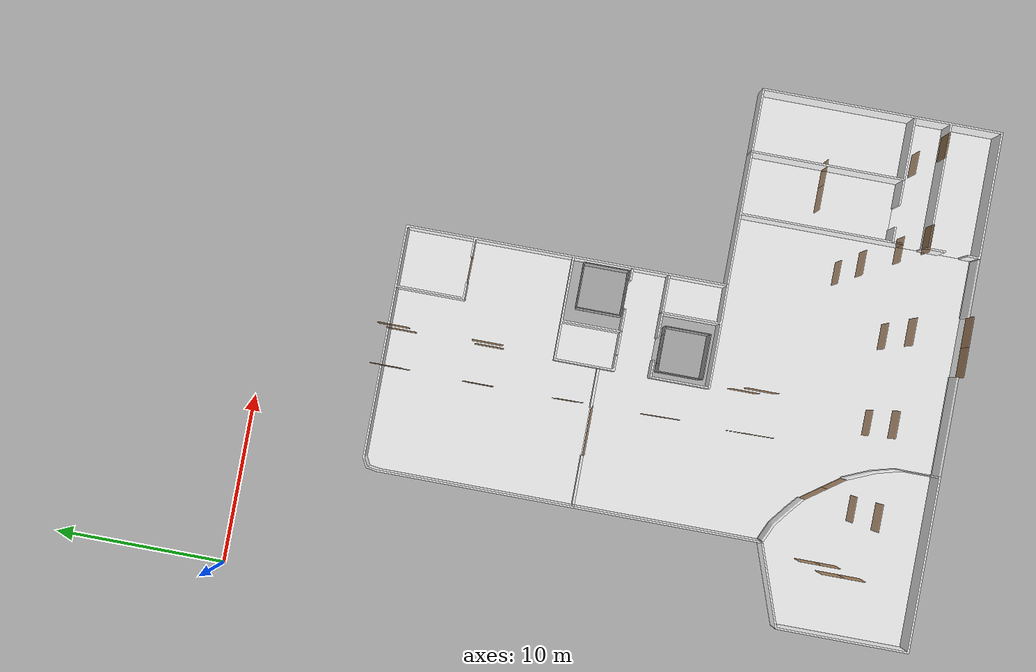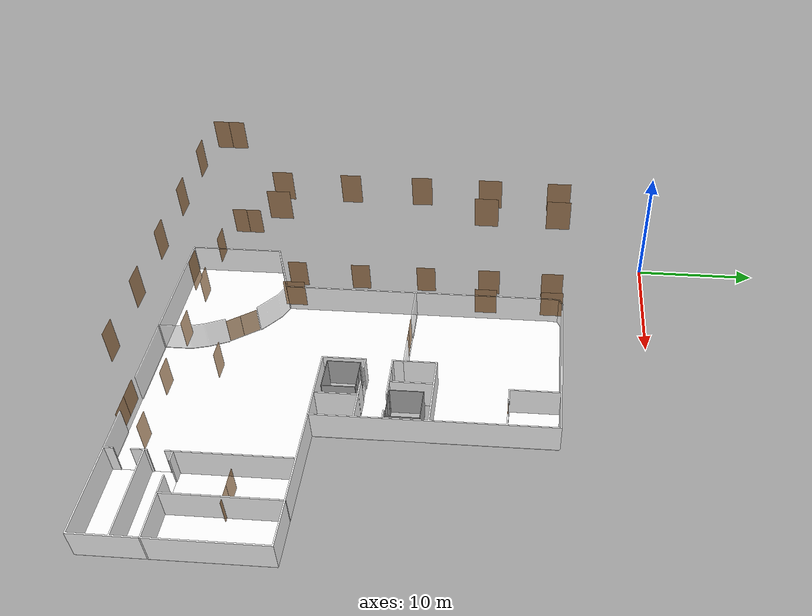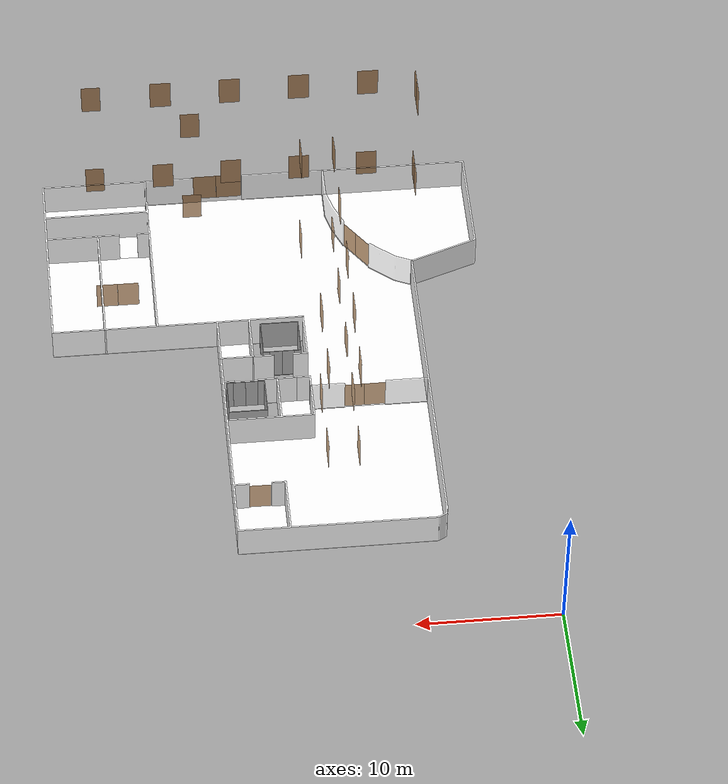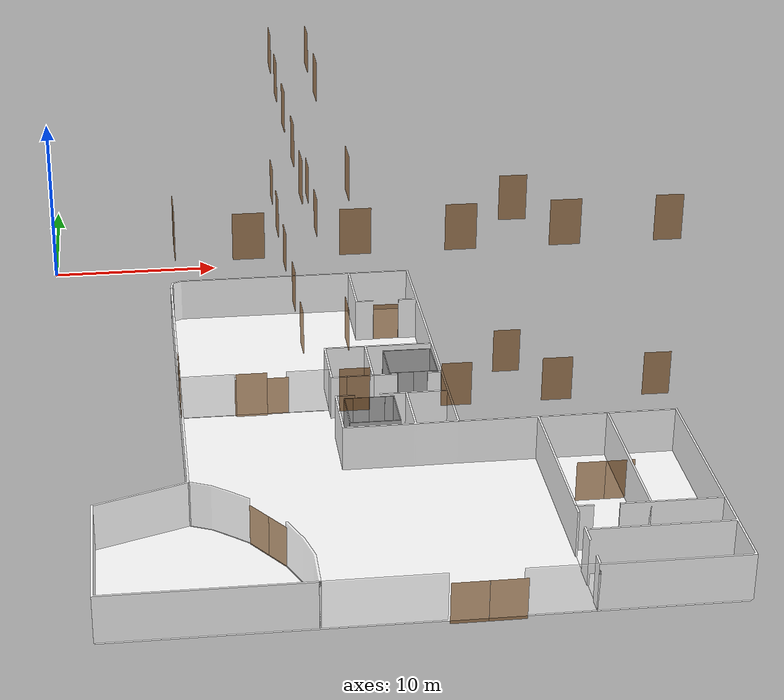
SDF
<sdf version="1.7">
 <world name="world">
  <physics type="ode">
   <max_step_size>0.001</max_step_size>
   <real_time_update_rate>1000</real_time_update_rate>
   <ode>
    <solver><iters>150</iters><sor>1.3</sor></solver>
    <constraints><erp>0.2</erp><cfm>0.0</cfm></constraints>
   </ode>
  </physics>
  <scene><ambient>0.8 0.8 0.8 1.0</ambient><background>0 0 0</background><grid>false</grid></scene>
  <include><uri>model://sun</uri></include>
  <model name="L1_door1">
   <pose>10.753654762321071 -33.79999264551465 0.0 0 0 2.1904910296829736</pose>
   <link name="right">
    <pose>0.7204413525969184 0 1.11 0 0 0</pose>
    <visual name="right_visual">
     <geometry><box><size>1.4308827051938369 0.03 2.2</size></box></geometry>
     <material><ambient>0.5 0.25 0 0.6</ambient><diffuse>0.5 0.25 0 0.6</diffuse></material>
    </visual>
    <collision name="right_collision">
     <geometry><box><size>1.4308827051938369 0.03 2.2</size></box></geometry>
     <surface><contact><collide_bitmask>0x02</collide_bitmask></contact></surface>
    </collision>
    <inertial>
     <mass>50.0</mass>
     <inertia><ixx>20.17041666666667</ixx><iyy>28.69760548342847</iyy><izz>8.534688816761804</izz></inertia>
    </inertial>
   </link>
   <joint name="right_joint" type="revolute">
    <parent>world</parent>
    <child>right</child>
    <axis><xyz>0 0 1</xyz><limit><lower>0</lower><upper>1.57</upper></limit></axis>
    <pose>0.7204413525969184 0 0 0 0 0</pose>
   </joint>
   <link name="left">
    <pose>-0.7204413525969184 0 1.11 0 0 0</pose>
    <visual name="left_visual">
     <geometry><box><size>1.4308827051938369 0.03 2.2</size></box></geometry>
     <material><ambient>0.5 0.25 0 0.6</ambient><diffuse>0.5 0.25 0 0.6</diffuse></material>
    </visual>
    <collision name="left_collision">
     <geometry><box><size>1.4308827051938369 0.03 2.2</size></box></geometry>
     <surface><contact><collide_bitmask>0x02</collide_bitmask></contact></surface>
    </collision>
    <inertial>
     <mass>50.0</mass>
     <inertia><ixx>20.17041666666667</ixx><iyy>28.69760548342847</iyy><izz>8.534688816761804</izz></inertia>
    </inertial>
   </link>
   <joint name="left_joint" type="revolute">
    <parent>world</parent>
    <child>left</child>
    <axis><xyz>0 0 1</xyz><limit><lower>-1.57</lower><upper>0</upper></limit></axis>
    <pose>-0.7204413525969184 0 0 0 0 0</pose>
   </joint>
  </model>
  <model name="L1_door2">
   <pose>11.515053553551752 -19.600764056030513 0.0 0 0 -3.1369488994516814</pose>
   <link name="right">
    <pose>0.7374085791900343 0 1.11 0 0 0</pose>
    <visual name="right_visual">
     <geometry><box><size>1.4648171583800687 0.03 2.2</size></box></geometry>
     <material><ambient>0.5 0.25 0 0.6</ambient><diffuse>0.5 0.25 0 0.6</diffuse></material>
    </visual>
    <collision name="right_collision">
     <geometry><box><size>1.4648171583800687 0.03 2.2</size></box></geometry>
     <surface><contact><collide_bitmask>0x02</collide_bitmask></contact></surface>
    </collision>
    <inertial>
     <mass>50.0</mass>
     <inertia><ixx>20.17041666666667</ixx><iyy>29.107038781186084</iyy><izz>8.944122114519415</izz></inertia>
    </inertial>
   </link>
   <joint name="right_joint" type="prismatic">
    <parent>world</parent>
    <child>right</child>
    <pose>0.7374085791900343 0 1.11 0 0 0</pose>
    <axis>
     <xyz>1 0 0</xyz>
     <limit>
      <lower>0.0</lower>
      <upper>1.4748171583800687</upper>
      <effort>500.0</effort>
      <velocity>0.8</velocity>
     </limit>
     <dynamics damping="60.0" friction="50.0"/>
    </axis>
   </joint>
   <link name="left">
    <pose>-0.7374085791900343 0 1.11 0 0 0</pose>
    <visual name="left_visual">
     <geometry><box><size>1.4648171583800687 0.03 2.2</size></box></geometry>
     <material><ambient>0.5 0.25 0 0.6</ambient><diffuse>0.5 0.25 0 0.6</diffuse></material>
    </visual>
    <collision name="left_collision">
     <geometry><box><size>1.4648171583800687 0.03 2.2</size></box></geometry>
     <surface><contact><collide_bitmask>0x02</collide_bitmask></contact></surface>
    </collision>
    <inertial>
     <mass>50.0</mass>
     <inertia><ixx>20.17041666666667</ixx><iyy>29.107038781186084</iyy><izz>8.944122114519415</izz></inertia>
    </inertial>
   </link>
   <joint name="left_joint" type="prismatic">
    <parent>world</parent>
    <child>left</child>
    <pose>-0.7374085791900343 0 1.11 0 0 0</pose>
    <axis>
     <xyz>1 0 0</xyz>
     <limit>
      <lower>-1.4748171583800687</lower>
      <upper>0.0</upper>
      <effort>500.0</effort>
      <velocity>0.8</velocity>
     </limit>
     <dynamics damping="60.0" friction="50.0"/>
    </axis>
   </joint>
   <plugin name="sliding_door" filename="libsliding_door_plugin.so">
    <ros><namespace>/doors/L1_door2</namespace></ros>
    <right_joint>right_joint</right_joint>
    <left_joint>left_joint</left_joint>
    <open_distance>1.3</open_distance>
    <kp>100.0</kp>
    <kd>120.0</kd>
   </plugin>
  </model>
  <model name="L1_door3">
   <pose>20.334155710474544 -40.40725483879361 0.0 0 0 -3.137402798278724</pose>
   <link name="right">
    <pose>0.9069965354571369 0 1.11 0 0 0</pose>
    <visual name="right_visual">
     <geometry><box><size>1.8039930709142737 0.03 2.2</size></box></geometry>
     <material><ambient>0.5 0.25 0 0.6</ambient><diffuse>0.5 0.25 0 0.6</diffuse></material>
    </visual>
    <collision name="right_collision">
     <geometry><box><size>1.8039930709142737 0.03 2.2</size></box></geometry>
     <surface><contact><collide_bitmask>0x02</collide_bitmask></contact></surface>
    </collision>
    <inertial>
     <mass>50.0</mass>
     <inertia><ixx>20.17041666666667</ixx><iyy>33.726629166277974</iyy><izz>13.563712499611302</izz></inertia>
    </inertial>
   </link>
   <joint name="right_joint" type="prismatic">
    <parent>world</parent>
    <child>right</child>
    <axis>
     <xyz>1 0 0</xyz>
     <limit>
      <lower>0.0</lower>
      <upper>1.4748171583800687</upper>
      <effort>500.0</effort>
      <velocity>0.8</velocity>
     </limit>
     <dynamics damping="60.0" friction="50.0"/>
    </axis>
   </joint>
   <link name="left">
    <pose>-0.9069965354571369 0 1.11 0 0 0</pose>
    <visual name="left_visual">
     <geometry><box><size>1.8039930709142737 0.03 2.2</size></box></geometry>
     <material><ambient>0.5 0.25 0 0.6</ambient><diffuse>0.5 0.25 0 0.6</diffuse></material>
    </visual>
    <collision name="left_collision">
     <geometry><box><size>1.8039930709142737 0.03 2.2</size></box></geometry>
     <surface><contact><collide_bitmask>0x02</collide_bitmask></contact></surface>
    </collision>
    <inertial>
     <mass>50.0</mass>
     <inertia><ixx>20.17041666666667</ixx><iyy>33.726629166277974</iyy><izz>13.563712499611302</izz></inertia>
    </inertial>
   </link>
   <joint name="left_joint" type="prismatic">
    <parent>world</parent>
    <child>left</child>
    <axis>
     <xyz>1 0 0</xyz>
     <limit>
      <lower>-1.4748171583800687</lower>
      <upper>0</upper>
      <effort>500.0</effort>
      <velocity>0.8</velocity>
     </limit>
     <dynamics damping="60.0" friction="50.0"/>
    </axis>
   </joint>
   <plugin name="sliding_door" filename="libsliding_door_plugin.so">
    <ros><namespace>/doors/L1_door3</namespace></ros>
    <right_joint>right_joint</right_joint>
    <left_joint>left_joint</left_joint>
    <open_distance>1.3</open_distance>
    <kp>100.0</kp>
    <kd>120.0</kd>
   </plugin>
  </model>
  <model name="L1_door4">
   <pose>19.549120677562087 -11.10939551168469 0.0 0 0 -0.009497018345977264</pose>
   <link name="right">
    <pose>0 0 1.11 0 0 0</pose>
    <visual name="right_visual">
     <geometry><box><size>1.5905993122484277 0.03 2.2</size></box></geometry>
     <material><ambient>0.5 0.25 0 0.6</ambient><diffuse>0.5 0.25 0 0.6</diffuse></material>
    </visual>
    <collision name="right_collision">
     <geometry><box><size>1.5905993122484277 0.03 2.2</size></box></geometry>
     <surface><contact><collide_bitmask>0x02</collide_bitmask></contact></surface>
    </collision>
    <inertial>
     <mass>50.0</mass>
     <inertia><ixx>20.17041666666667</ixx><iyy>30.70835905052155</iyy><izz>10.545442383854882</izz></inertia>
    </inertial>
   </link>
   <joint name="right_joint" type="revolute">
    <parent>world</parent>
    <child>right</child>
    <axis><xyz>0 0 1</xyz><limit><lower>0</lower><upper>1.57</upper></limit></axis>
    <pose>0.8002996561242138 0 0 0 0 0</pose>
   </joint>
  </model>
  <model name="L1_door5">
   <pose>28.079493196697264 -30.43738230505557 0.0 0 0 -0.0023958500301941633</pose>
   <link name="right">
    <pose>0.7494993011996198 0 1.11 0 0 0</pose>
    <visual name="right_visual">
     <geometry><box><size>1.4889986023992396 0.03 2.2</size></box></geometry>
     <material><ambient>0.5 0.25 0 0.6</ambient><diffuse>0.5 0.25 0 0.6</diffuse></material>
    </visual>
    <collision name="right_collision">
     <geometry><box><size>1.4889986023992396 0.03 2.2</size></box></geometry>
     <surface><contact><collide_bitmask>0x02</collide_bitmask></contact></surface>
    </collision>
    <inertial>
     <mass>50.0</mass>
     <inertia><ixx>20.17041666666667</ixx><iyy>29.404653491445373</iyy><izz>9.241736824778705</izz></inertia>
    </inertial>
   </link>
   <joint name="right_joint" type="prismatic">
    <parent>world</parent>
    <child>right</child>
    <axis>
     <xyz>1 0 0</xyz>
     <limit>
      <lower>0.0</lower>
      <upper>1.4748171583800687</upper>
      <effort>500.0</effort>
      <velocity>0.8</velocity>
     </limit>
     <dynamics damping="60.0" friction="50.0"/>
    </axis>
   </joint>
   <link name="left">
    <pose>-0.7494993011996198 0 1.11 0 0 0</pose>
    <visual name="left_visual">
     <geometry><box><size>1.4889986023992396 0.03 2.2</size></box></geometry>
     <material><ambient>0.5 0.25 0 0.6</ambient><diffuse>0.5 0.25 0 0.6</diffuse></material>
    </visual>
    <collision name="left_collision">
     <geometry><box><size>1.4889986023992396 0.03 2.2</size></box></geometry>
     <surface><contact><collide_bitmask>0x02</collide_bitmask></contact></surface>
    </collision>
    <inertial>
     <mass>50.0</mass>
     <inertia><ixx>20.17041666666667</ixx><iyy>29.404653491445373</iyy><izz>9.241736824778705</izz></inertia>
    </inertial>
   </link>
   <joint name="left_joint" type="prismatic">
    <parent>world</parent>
    <child>left</child>
    <axis>
     <xyz>1 0 0</xyz>
     <limit>
      <lower>-1.4748171583800687</lower>
      <upper>0</upper>
      <effort>500.0</effort>
      <velocity>0.8</velocity>
     </limit>
     <dynamics damping="60.0" friction="50.0"/>
    </axis>
   </joint>
   <plugin name="sliding_door" filename="libsliding_door_plugin.so">
    <ros><namespace>/doors/L1_door5</namespace></ros>
    <right_joint>right_joint</right_joint>
    <left_joint>left_joint</left_joint>
    <open_distance>1.3</open_distance>
    <kp>100.0</kp>
    <kd>120.0</kd>
   </plugin>
  </model>
  <include><name>hotel_L1</name><uri>model://hotel_L1</uri></include>
  <model name="L2_door2">
   <pose>6.76857286388343 -32.90682600516501 8.0 0 0 1.571612558028263</pose>
   <link name="right">
    <pose>0.5675078680191911 0 1.11 0 0 0</pose>
    <visual name="right_visual">
     <geometry><box><size>1.1250157360383821 0.03 2.2</size></box></geometry>
     <material><ambient>0.5 0.25 0 0.6</ambient><diffuse>0.5 0.25 0 0.6</diffuse></material>
    </visual>
    <collision name="right_collision">
     <geometry><box><size>1.1250157360383821 0.03 2.2</size></box></geometry>
     <surface><contact><collide_bitmask>0x02</collide_bitmask></contact></surface>
    </collision>
    <inertial>
     <mass>50.0</mass>
     <inertia><ixx>20.17041666666667</ixx><iyy>25.44025169305827</iyy><izz>5.277335026391595</izz></inertia>
    </inertial>
   </link>
   <joint name="right_joint" type="revolute">
    <parent>world</parent>
    <child>right</child>
    <axis><xyz>0 0 -1</xyz><limit><lower>0</lower><upper>1.57</upper></limit></axis>
    <pose>0.5675078680191911 0 0 0 0 0</pose>
   </joint>
   <link name="left">
    <pose>-0.5675078680191911 0 1.11 0 0 0</pose>
    <visual name="left_visual">
     <geometry><box><size>1.1250157360383821 0.03 2.2</size></box></geometry>
     <material><ambient>0.5 0.25 0 0.6</ambient><diffuse>0.5 0.25 0 0.6</diffuse></material>
    </visual>
    <collision name="left_collision">
     <geometry><box><size>1.1250157360383821 0.03 2.2</size></box></geometry>
     <surface><contact><collide_bitmask>0x02</collide_bitmask></contact></surface>
    </collision>
    <inertial>
     <mass>50.0</mass>
     <inertia><ixx>20.17041666666667</ixx><iyy>25.44025169305827</iyy><izz>5.277335026391595</izz></inertia>
    </inertial>
   </link>
   <joint name="left_joint" type="revolute">
    <parent>world</parent>
    <child>left</child>
    <axis><xyz>0 0 -1</xyz><limit><lower>-1.57</lower><upper>0</upper></limit></axis>
    <pose>-0.5675078680191911 0 0 0 0 0</pose>
   </joint>
  </model>
  <model name="L2_door3">
   <pose>10.044220258 -34.21478433126707 8.0 0 0 3.1365461417546308</pose>
   <link name="right">
    <pose>0 0 1.11 0 0 0</pose>
    <visual name="right_visual">
     <geometry><box><size>1.4278667928054123 0.03 2.2</size></box></geometry>
     <material><ambient>0.5 0.25 0 0.6</ambient><diffuse>0.5 0.25 0 0.6</diffuse></material>
    </visual>
    <collision name="right_collision">
     <geometry><box><size>1.4278667928054123 0.03 2.2</size></box></geometry>
     <surface><contact><collide_bitmask>0x02</collide_bitmask></contact></surface>
    </collision>
    <inertial>
     <mass>50.0</mass>
     <inertia><ixx>20.17041666666667</ixx><iyy>28.661681574985064</iyy><izz>8.498764908318392</izz></inertia>
    </inertial>
   </link>
   <joint name="right_joint" type="revolute">
    <parent>world</parent>
    <child>right</child>
    <axis><xyz>0 0 -1</xyz><limit><lower>0</lower><upper>1.57</upper></limit></axis>
    <pose>0.7189333964027061 0 0 0 0 0</pose>
   </joint>
  </model>
  <model name="L2_door4">
   <pose>19.62055855578882 -34.21478433126707 8.0 0 0 3.1365461417546308</pose>
   <link name="right">
    <pose>0 0 1.11 0 0 0</pose>
    <visual name="right_visual">
     <geometry><box><size>1.4278667928054123 0.03 2.2</size></box></geometry>
     <material><ambient>0.5 0.25 0 0.6</ambient><diffuse>0.5 0.25 0 0.6</diffuse></material>
    </visual>
    <collision name="right_collision">
     <geometry><box><size>1.4278667928054123 0.03 2.2</size></box></geometry>
     <surface><contact><collide_bitmask>0x02</collide_bitmask></contact></surface>
    </collision>
    <inertial>
     <mass>50.0</mass>
     <inertia><ixx>20.17041666666667</ixx><iyy>28.661681574985064</iyy><izz>8.498764908318392</izz></inertia>
    </inertial>
   </link>
   <joint name="right_joint" type="revolute">
    <parent>world</parent>
    <child>right</child>
    <axis><xyz>0 0 -1</xyz><limit><lower>0</lower><upper>1.57</upper></limit></axis>
    <pose>0.7189333964027061 0 0 0 0 0</pose>
   </joint>
  </model>
  <model name="L2_door5">
   <pose>14.832389407 -34.21478433126707 8.0 0 0 3.1365461417546308</pose>
   <link name="right">
    <pose>0 0 1.11 0 0 0</pose>
    <visual name="right_visual">
     <geometry><box><size>1.4278667928054123 0.03 2.2</size></box></geometry>
     <material><ambient>0.5 0.25 0 0.6</ambient><diffuse>0.5 0.25 0 0.6</diffuse></material>
    </visual>
    <collision name="right_collision">
     <geometry><box><size>1.4278667928054123 0.03 2.2</size></box></geometry>
     <surface><contact><collide_bitmask>0x02</collide_bitmask></contact></surface>
    </collision>
    <inertial>
     <mass>50.0</mass>
     <inertia><ixx>20.17041666666667</ixx><iyy>28.661681574985064</iyy><izz>8.498764908318392</izz></inertia>
    </inertial>
   </link>
   <joint name="right_joint" type="revolute">
    <parent>world</parent>
    <child>right</child>
    <axis><xyz>0 0 -1</xyz><limit><lower>0</lower><upper>1.57</upper></limit></axis>
    <pose>0.7189333964027061 0 0 0 0 0</pose>
   </joint>
  </model>
  <model name="L2_door6">
   <pose>24.408727706 -34.21478433126707 8.0 0 0 3.1365461417546308</pose>
   <link name="right">
    <pose>0 0 1.11 0 0 0</pose>
    <visual name="right_visual">
     <geometry><box><size>1.4278667928054123 0.03 2.2</size></box></geometry>
     <material><ambient>0.5 0.25 0 0.6</ambient><diffuse>0.5 0.25 0 0.6</diffuse></material>
    </visual>
    <collision name="right_collision">
     <geometry><box><size>1.4278667928054123 0.03 2.2</size></box></geometry>
     <surface><contact><collide_bitmask>0x02</collide_bitmask></contact></surface>
    </collision>
    <inertial>
     <mass>50.0</mass>
     <inertia><ixx>20.17041666666667</ixx><iyy>28.661681574985064</iyy><izz>8.498764908318392</izz></inertia>
    </inertial>
   </link>
   <joint name="right_joint" type="revolute">
    <parent>world</parent>
    <child>right</child>
    <axis><xyz>0 0 -1</xyz><limit><lower>0</lower><upper>1.57</upper></limit></axis>
    <pose>0.7189333964027061 0 0 0 0 0</pose>
   </joint>
  </model>
  <model name="L2_door7">
   <pose>13.018848337594756 -27.49809116 8.0 0 0 1.5874688733681936</pose>
   <link name="right">
    <pose>0 0 1.11 0 0 0</pose>
    <visual name="right_visual">
     <geometry><box><size>1.382945881897145 0.03 2.2</size></box></geometry>
     <material><ambient>0.5 0.25 0 0.6</ambient><diffuse>0.5 0.25 0 0.6</diffuse></material>
    </visual>
    <collision name="right_collision">
     <geometry><box><size>1.382945881897145 0.03 2.2</size></box></geometry>
     <surface><contact><collide_bitmask>0x02</collide_bitmask></contact></surface>
    </collision>
    <inertial>
     <mass>50.0</mass>
     <inertia><ixx>20.17041666666667</ixx><iyy>28.13558046773447</iyy><izz>7.9726638010677995</izz></inertia>
    </inertial>
   </link>
   <joint name="right_joint" type="revolute">
    <parent>world</parent>
    <child>right</child>
    <axis><xyz>0 0 -1</xyz><limit><lower>0</lower><upper>1.57</upper></limit></axis>
    <pose>0.6964729409485725 0 0 0 0 0</pose>
   </joint>
  </model>
  <model name="L2_door8">
   <pose>13.05848337594756 -22.704836665 8.0 0 0 1.5874688733681936</pose>
   <link name="right">
    <pose>0 0 1.11 0 0 0</pose>
    <visual name="right_visual">
     <geometry><box><size>1.382945881897145 0.03 2.2</size></box></geometry>
     <material><ambient>0.5 0.25 0 0.6</ambient><diffuse>0.5 0.25 0 0.6</diffuse></material>
    </visual>
    <collision name="right_collision">
     <geometry><box><size>1.382945881897145 0.03 2.2</size></box></geometry>
     <surface><contact><collide_bitmask>0x02</collide_bitmask></contact></surface>
    </collision>
    <inertial>
     <mass>50.0</mass>
     <inertia><ixx>20.17041666666667</ixx><iyy>28.13558046773447</iyy><izz>7.9726638010677995</izz></inertia>
    </inertial>
   </link>
   <joint name="right_joint" type="revolute">
    <parent>world</parent>
    <child>right</child>
    <axis><xyz>0 0 -1</xyz><limit><lower>0</lower><upper>1.57</upper></limit></axis>
    <pose>0.6964729409485725 0 0 0 0 0</pose>
   </joint>
  </model>
  <model name="L2_door9">
   <pose>13.018848337594756 -17.76158217016259 8.0 0 0 1.5874688733681936</pose>
   <link name="right">
    <pose>0 0 1.11 0 0 0</pose>
    <visual name="right_visual">
     <geometry><box><size>1.382945881897145 0.03 2.2</size></box></geometry>
     <material><ambient>0.5 0.25 0 0.6</ambient><diffuse>0.5 0.25 0 0.6</diffuse></material>
    </visual>
    <collision name="right_collision">
     <geometry><box><size>1.382945881897145 0.03 2.2</size></box></geometry>
     <surface><contact><collide_bitmask>0x02</collide_bitmask></contact></surface>
    </collision>
    <inertial>
     <mass>50.0</mass>
     <inertia><ixx>20.17041666666667</ixx><iyy>28.13558046773447</iyy><izz>7.9726638010677995</izz></inertia>
    </inertial>
   </link>
   <joint name="right_joint" type="revolute">
    <parent>world</parent>
    <child>right</child>
    <axis><xyz>0 0 -1</xyz><limit><lower>0</lower><upper>1.57</upper></limit></axis>
    <pose>0.6964729409485725 0 0 0 0 0</pose>
   </joint>
  </model>
  <model name="L2_door11">
   <pose>13.070832545372092 -8.29507317951618 8.0 0 0 1.571612558028263</pose>
   <link name="right">
    <pose>0 0 1.11 0 0 0</pose>
    <visual name="right_visual">
     <geometry><box><size>1.5950330216253457 0.03 2.2</size></box></geometry>
     <material><ambient>0.5 0.25 0 0.6</ambient><diffuse>0.5 0.25 0 0.6</diffuse></material>
    </visual>
    <collision name="right_collision">
     <geometry><box><size>1.5950330216253457 0.03 2.2</size></box></geometry>
     <surface><contact><collide_bitmask>0x02</collide_bitmask></contact></surface>
    </collision>
    <inertial>
     <mass>50.0</mass>
     <inertia><ixx>20.17041666666667</ixx><iyy>30.767209750313672</iyy><izz>10.604293083647002</izz></inertia>
    </inertial>
   </link>
   <joint name="right_joint" type="revolute">
    <parent>world</parent>
    <child>right</child>
    <axis><xyz>0 0 -1</xyz><limit><lower>0</lower><upper>1.57</upper></limit></axis>
    <pose>0.8025165108126728 0 0 0 0 0</pose>
   </joint>
  </model>
  <model name="L2_door12">
   <pose>15.28470442617677 -27.2761317707633 8.0 0 0 1.571612558028262</pose>
   <link name="right">
    <pose>0 0 1.11 0 0 0</pose>
    <visual name="right_visual">
     <geometry><box><size>1.5658659299508506 0.03 2.2</size></box></geometry>
     <material><ambient>0.5 0.25 0 0.6</ambient><diffuse>0.5 0.25 0 0.6</diffuse></material>
    </visual>
    <collision name="right_collision">
     <geometry><box><size>1.5658659299508506 0.03 2.2</size></box></geometry>
     <surface><contact><collide_bitmask>0x02</collide_bitmask></contact></surface>
    </collision>
    <inertial>
     <mass>50.0</mass>
     <inertia><ixx>20.17041666666667</ixx><iyy>30.38306712742018</iyy><izz>10.22015046075351</izz></inertia>
    </inertial>
   </link>
   <joint name="right_joint" type="revolute">
    <parent>world</parent>
    <child>right</child>
    <axis><xyz>0 0 1</xyz><limit><lower>0</lower><upper>1.57</upper></limit></axis>
    <pose>0.7879329649754253 0 0 0 0 0</pose>
   </joint>
  </model>
  <model name="L2_door14">
   <pose>22.582882547846204 -31.092638612981972 8.0 0 0 3.137779488569298</pose>
   <link name="right">
    <pose>0 0 1.11 0 0 0</pose>
    <visual name="right_visual">
     <geometry><box><size>1.2889329745237348 0.03 2.2</size></box></geometry>
     <material><ambient>0.5 0.25 0 0.6</ambient><diffuse>0.5 0.25 0 0.6</diffuse></material>
    </visual>
    <collision name="right_collision">
     <geometry><box><size>1.2889329745237348 0.03 2.2</size></box></geometry>
     <surface><contact><collide_bitmask>0x02</collide_bitmask></contact></surface>
    </collision>
    <inertial>
     <mass>50.0</mass>
     <inertia><ixx>20.17041666666667</ixx><iyy>27.088950886727517</iyy><izz>6.926034220060845</izz></inertia>
    </inertial>
   </link>
   <joint name="right_joint" type="revolute">
    <parent>world</parent>
    <child>right</child>
    <axis><xyz>0 0 1</xyz><limit><lower>0</lower><upper>1.57</upper></limit></axis>
    <pose>0.6494664872618674 0 0 0 0 0</pose>
   </joint>
  </model>
  <model name="L2_door15">
   <pose>29.19689685453295 -34.1844883615378 8.0 0 0 3.1287318603676484</pose>
   <link name="right">
    <pose>0 0 1.11 0 0 0</pose>
    <visual name="right_visual">
     <geometry><box><size>1.2884785147293154 0.03 2.2</size></box></geometry>
     <material><ambient>0.5 0.25 0 0.6</ambient><diffuse>0.5 0.25 0 0.6</diffuse></material>
    </visual>
    <collision name="right_collision">
     <geometry><box><size>1.2884785147293154 0.03 2.2</size></box></geometry>
     <surface><contact><collide_bitmask>0x02</collide_bitmask></contact></surface>
    </collision>
    <inertial>
     <mass>50.0</mass>
     <inertia><ixx>20.17041666666667</ixx><iyy>27.0840703454961</iyy><izz>6.921153678829428</izz></inertia>
    </inertial>
   </link>
   <joint name="right_joint" type="revolute">
    <parent>world</parent>
    <child>right</child>
    <axis><xyz>0 0 -1</xyz><limit><lower>0</lower><upper>1.57</upper></limit></axis>
    <pose>0.6492392573646577 0 0 0 0 0</pose>
   </joint>
  </model>
  <model name="L2_door16">
   <pose>15.15470442617677 -8.29507317951618 8.0 0 0 1.571612558028263</pose>
   <link name="right">
    <pose>0 0 1.11 0 0 0</pose>
    <visual name="right_visual">
     <geometry><box><size>1.5950330216253457 0.03 2.2</size></box></geometry>
     <material><ambient>0.5 0.25 0 0.6</ambient><diffuse>0.5 0.25 0 0.6</diffuse></material>
    </visual>
    <collision name="right_collision">
     <geometry><box><size>1.5950330216253457 0.03 2.2</size></box></geometry>
     <surface><contact><collide_bitmask>0x02</collide_bitmask></contact></surface>
    </collision>
    <inertial>
     <mass>50.0</mass>
     <inertia><ixx>20.17041666666667</ixx><iyy>30.767209750313672</iyy><izz>10.604293083647002</izz></inertia>
    </inertial>
   </link>
   <joint name="right_joint" type="revolute">
    <parent>world</parent>
    <child>right</child>
    <axis><xyz>0 0 -1</xyz><limit><lower>0</lower><upper>1.57</upper></limit></axis>
    <pose>0.8025165108126728 0 0 0 0 0</pose>
   </joint>
  </model>
  <model name="L2_door17">
   <pose>13.010832545372092 -13.028327675 8.0 0 0 1.571612558028263</pose>
   <link name="right">
    <pose>0 0 1.11 0 0 0</pose>
    <visual name="right_visual">
     <geometry><box><size>1.5950330216253457 0.03 2.2</size></box></geometry>
     <material><ambient>0.5 0.25 0 0.6</ambient><diffuse>0.5 0.25 0 0.6</diffuse></material>
    </visual>
    <collision name="right_collision">
     <geometry><box><size>1.5950330216253457 0.03 2.2</size></box></geometry>
     <surface><contact><collide_bitmask>0x02</collide_bitmask></contact></surface>
    </collision>
    <inertial>
     <mass>50.0</mass>
     <inertia><ixx>20.17041666666667</ixx><iyy>30.767209750313672</iyy><izz>10.604293083647002</izz></inertia>
    </inertial>
   </link>
   <joint name="right_joint" type="revolute">
    <parent>world</parent>
    <child>right</child>
    <axis><xyz>0 0 -1</xyz><limit><lower>0</lower><upper>1.57</upper></limit></axis>
    <pose>0.8025165108126728 0 0 0 0 0</pose>
   </joint>
  </model>
  <model name="L2_door18">
   <pose>15.15470442617677 -13.148327675 8.0 0 0 1.571612558028263</pose>
   <link name="right">
    <pose>0 0 1.11 0 0 0</pose>
    <visual name="right_visual">
     <geometry><box><size>1.5950330216253457 0.03 2.2</size></box></geometry>
     <material><ambient>0.5 0.25 0 0.6</ambient><diffuse>0.5 0.25 0 0.6</diffuse></material>
    </visual>
    <collision name="right_collision">
     <geometry><box><size>1.5950330216253457 0.03 2.2</size></box></geometry>
     <surface><contact><collide_bitmask>0x02</collide_bitmask></contact></surface>
    </collision>
    <inertial>
     <mass>50.0</mass>
     <inertia><ixx>20.17041666666667</ixx><iyy>30.767209750313672</iyy><izz>10.604293083647002</izz></inertia>
    </inertial>
   </link>
   <joint name="right_joint" type="revolute">
    <parent>world</parent>
    <child>right</child>
    <axis><xyz>0 0 -1</xyz><limit><lower>0</lower><upper>1.57</upper></limit></axis>
    <pose>0.8025165108126728 0 0 0 0 0</pose>
   </joint>
  </model>
  <model name="L3_door2">
   <pose>6.76857286388343 -32.90682600516501 16.0 0 0 1.571612558028263</pose>
   <link name="right">
    <pose>0.5675078680191911 0 1.11 0 0 0</pose>
    <visual name="right_visual">
     <geometry><box><size>1.1250157360383821 0.03 2.2</size></box></geometry>
     <material><ambient>0.5 0.25 0 0.6</ambient><diffuse>0.5 0.25 0 0.6</diffuse></material>
    </visual>
    <collision name="right_collision">
     <geometry><box><size>1.1250157360383821 0.03 2.2</size></box></geometry>
     <surface><contact><collide_bitmask>0x02</collide_bitmask></contact></surface>
    </collision>
    <inertial>
     <mass>50.0</mass>
     <inertia><ixx>20.17041666666667</ixx><iyy>25.44025169305827</iyy><izz>5.277335026391595</izz></inertia>
    </inertial>
   </link>
   <joint name="right_joint" type="revolute">
    <parent>world</parent>
    <child>right</child>
    <axis><xyz>0 0 -1</xyz><limit><lower>0</lower><upper>1.57</upper></limit></axis>
    <pose>0.5675078680191911 0 0 0 0 0</pose>
   </joint>
   <link name="left">
    <pose>-0.5675078680191911 0 1.11 0 0 0</pose>
    <visual name="left_visual">
     <geometry><box><size>1.1250157360383821 0.03 2.2</size></box></geometry>
     <material><ambient>0.5 0.25 0 0.6</ambient><diffuse>0.5 0.25 0 0.6</diffuse></material>
    </visual>
    <collision name="left_collision">
     <geometry><box><size>1.1250157360383821 0.03 2.2</size></box></geometry>
     <surface><contact><collide_bitmask>0x02</collide_bitmask></contact></surface>
    </collision>
    <inertial>
     <mass>50.0</mass>
     <inertia><ixx>20.17041666666667</ixx><iyy>25.44025169305827</iyy><izz>5.277335026391595</izz></inertia>
    </inertial>
   </link>
   <joint name="left_joint" type="revolute">
    <parent>world</parent>
    <child>left</child>
    <axis><xyz>0 0 -1</xyz><limit><lower>-1.57</lower><upper>0</upper></limit></axis>
    <pose>-0.5675078680191911 0 0 0 0 0</pose>
   </joint>
  </model>
  <model name="L3_door3">
   <pose>10.044220258 -34.21478433126707 16.0 0 0 3.1365461417546308</pose>
   <link name="right">
    <pose>0 0 1.11 0 0 0</pose>
    <visual name="right_visual">
     <geometry><box><size>1.4278667928054123 0.03 2.2</size></box></geometry>
     <material><ambient>0.5 0.25 0 0.6</ambient><diffuse>0.5 0.25 0 0.6</diffuse></material>
    </visual>
    <collision name="right_collision">
     <geometry><box><size>1.4278667928054123 0.03 2.2</size></box></geometry>
     <surface><contact><collide_bitmask>0x02</collide_bitmask></contact></surface>
    </collision>
    <inertial>
     <mass>50.0</mass>
     <inertia><ixx>20.17041666666667</ixx><iyy>28.661681574985064</iyy><izz>8.498764908318392</izz></inertia>
    </inertial>
   </link>
   <joint name="right_joint" type="revolute">
    <parent>world</parent>
    <child>right</child>
    <axis><xyz>0 0 -1</xyz><limit><lower>0</lower><upper>1.57</upper></limit></axis>
    <pose>0.7189333964027061 0 0 0 0 0</pose>
   </joint>
  </model>
  <model name="L3_door4">
   <pose>19.62055855578882 -34.21478433126707 16.0 0 0 3.1365461417546308</pose>
   <link name="right">
    <pose>0 0 1.11 0 0 0</pose>
    <visual name="right_visual">
     <geometry><box><size>1.4278667928054123 0.03 2.2</size></box></geometry>
     <material><ambient>0.5 0.25 0 0.6</ambient><diffuse>0.5 0.25 0 0.6</diffuse></material>
    </visual>
    <collision name="right_collision">
     <geometry><box><size>1.4278667928054123 0.03 2.2</size></box></geometry>
     <surface><contact><collide_bitmask>0x02</collide_bitmask></contact></surface>
    </collision>
    <inertial>
     <mass>50.0</mass>
     <inertia><ixx>20.17041666666667</ixx><iyy>28.661681574985064</iyy><izz>8.498764908318392</izz></inertia>
    </inertial>
   </link>
   <joint name="right_joint" type="revolute">
    <parent>world</parent>
    <child>right</child>
    <axis><xyz>0 0 -1</xyz><limit><lower>0</lower><upper>1.57</upper></limit></axis>
    <pose>0.7189333964027061 0 0 0 0 0</pose>
   </joint>
  </model>
  <model name="L3_door5">
   <pose>14.832389407 -34.21478433126707 16.0 0 0 3.1365461417546308</pose>
   <link name="right">
    <pose>0 0 1.11 0 0 0</pose>
    <visual name="right_visual">
     <geometry><box><size>1.4278667928054123 0.03 2.2</size></box></geometry>
     <material><ambient>0.5 0.25 0 0.6</ambient><diffuse>0.5 0.25 0 0.6</diffuse></material>
    </visual>
    <collision name="right_collision">
     <geometry><box><size>1.4278667928054123 0.03 2.2</size></box></geometry>
     <surface><contact><collide_bitmask>0x02</collide_bitmask></contact></surface>
    </collision>
    <inertial>
     <mass>50.0</mass>
     <inertia><ixx>20.17041666666667</ixx><iyy>28.661681574985064</iyy><izz>8.498764908318392</izz></inertia>
    </inertial>
   </link>
   <joint name="right_joint" type="revolute">
    <parent>world</parent>
    <child>right</child>
    <axis><xyz>0 0 -1</xyz><limit><lower>0</lower><upper>1.57</upper></limit></axis>
    <pose>0.7189333964027061 0 0 0 0 0</pose>
   </joint>
  </model>
  <model name="L3_door6">
   <pose>24.408727706 -34.21478433126707 16.0 0 0 3.1365461417546308</pose>
   <link name="right">
    <pose>0 0 1.11 0 0 0</pose>
    <visual name="right_visual">
     <geometry><box><size>1.4278667928054123 0.03 2.2</size></box></geometry>
     <material><ambient>0.5 0.25 0 0.6</ambient><diffuse>0.5 0.25 0 0.6</diffuse></material>
    </visual>
    <collision name="right_collision">
     <geometry><box><size>1.4278667928054123 0.03 2.2</size></box></geometry>
     <surface><contact><collide_bitmask>0x02</collide_bitmask></contact></surface>
    </collision>
    <inertial>
     <mass>50.0</mass>
     <inertia><ixx>20.17041666666667</ixx><iyy>28.661681574985064</iyy><izz>8.498764908318392</izz></inertia>
    </inertial>
   </link>
   <joint name="right_joint" type="revolute">
    <parent>world</parent>
    <child>right</child>
    <axis><xyz>0 0 -1</xyz><limit><lower>0</lower><upper>1.57</upper></limit></axis>
    <pose>0.7189333964027061 0 0 0 0 0</pose>
   </joint>
  </model>
  <model name="L3_door7">
   <pose>13.018848337594756 -27.49809116 16.0 0 0 1.5874688733681936</pose>
   <link name="right">
    <pose>0 0 1.11 0 0 0</pose>
    <visual name="right_visual">
     <geometry><box><size>1.382945881897145 0.03 2.2</size></box></geometry>
     <material><ambient>0.5 0.25 0 0.6</ambient><diffuse>0.5 0.25 0 0.6</diffuse></material>
    </visual>
    <collision name="right_collision">
     <geometry><box><size>1.382945881897145 0.03 2.2</size></box></geometry>
     <surface><contact><collide_bitmask>0x02</collide_bitmask></contact></surface>
    </collision>
    <inertial>
     <mass>50.0</mass>
     <inertia><ixx>20.17041666666667</ixx><iyy>28.13558046773447</iyy><izz>7.9726638010677995</izz></inertia>
    </inertial>
   </link>
   <joint name="right_joint" type="revolute">
    <parent>world</parent>
    <child>right</child>
    <axis><xyz>0 0 -1</xyz><limit><lower>0</lower><upper>1.57</upper></limit></axis>
    <pose>0.6964729409485725 0 0 0 0 0</pose>
   </joint>
  </model>
  <model name="L3_door8">
   <pose>13.05848337594756 -22.704836665 16.0 0 0 1.5874688733681936</pose>
   <link name="right">
    <pose>0 0 1.11 0 0 0</pose>
    <visual name="right_visual">
     <geometry><box><size>1.382945881897145 0.03 2.2</size></box></geometry>
     <material><ambient>0.5 0.25 0 0.6</ambient><diffuse>0.5 0.25 0 0.6</diffuse></material>
    </visual>
    <collision name="right_collision">
     <geometry><box><size>1.382945881897145 0.03 2.2</size></box></geometry>
     <surface><contact><collide_bitmask>0x02</collide_bitmask></contact></surface>
    </collision>
    <inertial>
     <mass>50.0</mass>
     <inertia><ixx>20.17041666666667</ixx><iyy>28.13558046773447</iyy><izz>7.9726638010677995</izz></inertia>
    </inertial>
   </link>
   <joint name="right_joint" type="revolute">
    <parent>world</parent>
    <child>right</child>
    <axis><xyz>0 0 -1</xyz><limit><lower>0</lower><upper>1.57</upper></limit></axis>
    <pose>0.6964729409485725 0 0 0 0 0</pose>
   </joint>
  </model>
  <model name="L3_door9">
   <pose>13.018848337594756 -17.76158217016259 16.0 0 0 1.5874688733681936</pose>
   <link name="right">
    <pose>0 0 1.11 0 0 0</pose>
    <visual name="right_visual">
     <geometry><box><size>1.382945881897145 0.03 2.2</size></box></geometry>
     <material><ambient>0.5 0.25 0 0.6</ambient><diffuse>0.5 0.25 0 0.6</diffuse></material>
    </visual>
    <collision name="right_collision">
     <geometry><box><size>1.382945881897145 0.03 2.2</size></box></geometry>
     <surface><contact><collide_bitmask>0x02</collide_bitmask></contact></surface>
    </collision>
    <inertial>
     <mass>50.0</mass>
     <inertia><ixx>20.17041666666667</ixx><iyy>28.13558046773447</iyy><izz>7.9726638010677995</izz></inertia>
    </inertial>
   </link>
   <joint name="right_joint" type="revolute">
    <parent>world</parent>
    <child>right</child>
    <axis><xyz>0 0 -1</xyz><limit><lower>0</lower><upper>1.57</upper></limit></axis>
    <pose>0.6964729409485725 0 0 0 0 0</pose>
   </joint>
  </model>
  <model name="L3_door11">
   <pose>13.070832545372092 -8.29507317951618 16.0 0 0 1.571612558028263</pose>
   <link name="right">
    <pose>0 0 1.11 0 0 0</pose>
    <visual name="right_visual">
     <geometry><box><size>1.5950330216253457 0.03 2.2</size></box></geometry>
     <material><ambient>0.5 0.25 0 0.6</ambient><diffuse>0.5 0.25 0 0.6</diffuse></material>
    </visual>
    <collision name="right_collision">
     <geometry><box><size>1.5950330216253457 0.03 2.2</size></box></geometry>
     <surface><contact><collide_bitmask>0x02</collide_bitmask></contact></surface>
    </collision>
    <inertial>
     <mass>50.0</mass>
     <inertia><ixx>20.17041666666667</ixx><iyy>30.767209750313672</iyy><izz>10.604293083647002</izz></inertia>
    </inertial>
   </link>
   <joint name="right_joint" type="revolute">
    <parent>world</parent>
    <child>right</child>
    <axis><xyz>0 0 -1</xyz><limit><lower>0</lower><upper>1.57</upper></limit></axis>
    <pose>0.8025165108126728 0 0 0 0 0</pose>
   </joint>
  </model>
  <model name="L3_door12">
   <pose>15.28470442617677 -27.2761317707633 16.0 0 0 1.571612558028262</pose>
   <link name="right">
    <pose>0 0 1.11 0 0 0</pose>
    <visual name="right_visual">
     <geometry><box><size>1.5658659299508506 0.03 2.2</size></box></geometry>
     <material><ambient>0.5 0.25 0 0.6</ambient><diffuse>0.5 0.25 0 0.6</diffuse></material>
    </visual>
    <collision name="right_collision">
     <geometry><box><size>1.5658659299508506 0.03 2.2</size></box></geometry>
     <surface><contact><collide_bitmask>0x02</collide_bitmask></contact></surface>
    </collision>
    <inertial>
     <mass>50.0</mass>
     <inertia><ixx>20.17041666666667</ixx><iyy>30.38306712742018</iyy><izz>10.22015046075351</izz></inertia>
    </inertial>
   </link>
   <joint name="right_joint" type="revolute">
    <parent>world</parent>
    <child>right</child>
    <axis><xyz>0 0 1</xyz><limit><lower>0</lower><upper>1.57</upper></limit></axis>
    <pose>0.7879329649754253 0 0 0 0 0</pose>
   </joint>
  </model>
  <model name="L3_door14">
   <pose>22.582882547846204 -31.092638612981972 16.0 0 0 3.137779488569298</pose>
   <link name="right">
    <pose>0 0 1.11 0 0 0</pose>
    <visual name="right_visual">
     <geometry><box><size>1.2889329745237348 0.03 2.2</size></box></geometry>
     <material><ambient>0.5 0.25 0 0.6</ambient><diffuse>0.5 0.25 0 0.6</diffuse></material>
    </visual>
    <collision name="right_collision">
     <geometry><box><size>1.2889329745237348 0.03 2.2</size></box></geometry>
     <surface><contact><collide_bitmask>0x02</collide_bitmask></contact></surface>
    </collision>
    <inertial>
     <mass>50.0</mass>
     <inertia><ixx>20.17041666666667</ixx><iyy>27.088950886727517</iyy><izz>6.926034220060845</izz></inertia>
    </inertial>
   </link>
   <joint name="right_joint" type="revolute">
    <parent>world</parent>
    <child>right</child>
    <axis><xyz>0 0 1</xyz><limit><lower>0</lower><upper>1.57</upper></limit></axis>
    <pose>0.6494664872618674 0 0 0 0 0</pose>
   </joint>
  </model>
  <model name="L3_door15">
   <pose>29.19689685453295 -34.1844883615378 16.0 0 0 3.1287318603676484</pose>
   <link name="right">
    <pose>0 0 1.11 0 0 0</pose>
    <visual name="right_visual">
     <geometry><box><size>1.2884785147293154 0.03 2.2</size></box></geometry>
     <material><ambient>0.5 0.25 0 0.6</ambient><diffuse>0.5 0.25 0 0.6</diffuse></material>
    </visual>
    <collision name="right_collision">
     <geometry><box><size>1.2884785147293154 0.03 2.2</size></box></geometry>
     <surface><contact><collide_bitmask>0x02</collide_bitmask></contact></surface>
    </collision>
    <inertial>
     <mass>50.0</mass>
     <inertia><ixx>20.17041666666667</ixx><iyy>27.0840703454961</iyy><izz>6.921153678829428</izz></inertia>
    </inertial>
   </link>
   <joint name="right_joint" type="revolute">
    <parent>world</parent>
    <child>right</child>
    <axis><xyz>0 0 -1</xyz><limit><lower>0</lower><upper>1.57</upper></limit></axis>
    <pose>0.6492392573646577 0 0 0 0 0</pose>
   </joint>
  </model>
  <model name="L3_door16">
   <pose>15.15470442617677 -8.29507317951618 16.0 0 0 1.571612558028263</pose>
   <link name="right">
    <pose>0 0 1.11 0 0 0</pose>
    <visual name="right_visual">
     <geometry><box><size>1.5950330216253457 0.03 2.2</size></box></geometry>
     <material><ambient>0.5 0.25 0 0.6</ambient><diffuse>0.5 0.25 0 0.6</diffuse></material>
    </visual>
    <collision name="right_collision">
     <geometry><box><size>1.5950330216253457 0.03 2.2</size></box></geometry>
     <surface><contact><collide_bitmask>0x02</collide_bitmask></contact></surface>
    </collision>
    <inertial>
     <mass>50.0</mass>
     <inertia><ixx>20.17041666666667</ixx><iyy>30.767209750313672</iyy><izz>10.604293083647002</izz></inertia>
    </inertial>
   </link>
   <joint name="right_joint" type="revolute">
    <parent>world</parent>
    <child>right</child>
    <axis><xyz>0 0 -1</xyz><limit><lower>0</lower><upper>1.57</upper></limit></axis>
    <pose>0.8025165108126728 0 0 0 0 0</pose>
   </joint>
  </model>
  <model name="L3_door17">
   <pose>13.010832545372092 -13.028327675 16.0 0 0 1.571612558028263</pose>
   <link name="right">
    <pose>0 0 1.11 0 0 0</pose>
    <visual name="right_visual">
     <geometry><box><size>1.5950330216253457 0.03 2.2</size></box></geometry>
     <material><ambient>0.5 0.25 0 0.6</ambient><diffuse>0.5 0.25 0 0.6</diffuse></material>
    </visual>
    <collision name="right_collision">
     <geometry><box><size>1.5950330216253457 0.03 2.2</size></box></geometry>
     <surface><contact><collide_bitmask>0x02</collide_bitmask></contact></surface>
    </collision>
    <inertial>
     <mass>50.0</mass>
     <inertia><ixx>20.17041666666667</ixx><iyy>30.767209750313672</iyy><izz>10.604293083647002</izz></inertia>
    </inertial>
   </link>
   <joint name="right_joint" type="revolute">
    <parent>world</parent>
    <child>right</child>
    <axis><xyz>0 0 -1</xyz><limit><lower>0</lower><upper>1.57</upper></limit></axis>
    <pose>0.8025165108126728 0 0 0 0 0</pose>
   </joint>
  </model>
  <model name="L3_door18">
   <pose>15.15470442617677 -13.148327675 16.0 0 0 1.571612558028263</pose>
   <link name="right">
    <pose>0 0 1.11 0 0 0</pose>
    <visual name="right_visual">
     <geometry><box><size>1.5950330216253457 0.03 2.2</size></box></geometry>
     <material><ambient>0.5 0.25 0 0.6</ambient><diffuse>0.5 0.25 0 0.6</diffuse></material>
    </visual>
    <collision name="right_collision">
     <geometry><box><size>1.5950330216253457 0.03 2.2</size></box></geometry>
     <surface><contact><collide_bitmask>0x02</collide_bitmask></contact></surface>
    </collision>
    <inertial>
     <mass>50.0</mass>
     <inertia><ixx>20.17041666666667</ixx><iyy>30.767209750313672</iyy><izz>10.604293083647002</izz></inertia>
    </inertial>
   </link>
   <joint name="right_joint" type="revolute">
    <parent>world</parent>
    <child>right</child>
    <axis><xyz>0 0 -1</xyz><limit><lower>0</lower><upper>1.57</upper></limit></axis>
    <pose>0.8025165108126728 0 0 0 0 0</pose>
   </joint>
  </model>
  <model name="Lift1">
   <link name="platform">
    <gravity>false</gravity>
    <inertial>
     <mass>1200</mass>
     <inertia><ixx>729.2500000000001</ixx><iyy>729.2500000000001</iyy><izz>1458.0000000000002</izz></inertia>
    </inertial>
    <visual name="floor_visual">
     <pose>0 0 -0.025 0 0 0</pose>
     <geometry><box><size>2.7 2.7 0.05</size></box></geometry>
     <material>
      <ambient>0.5 0.5 0.5 1</ambient>
      <diffuse>0.7 0.7 0.7 1</diffuse>
      <specular>0.6 0.6 0.6 1</specular>
      <emissive>0.1 0.1 0.1 1</emissive>
     </material>
    </visual>
    <collision name="floor_collision">
     <pose>0 0 -0.025 0 0 0</pose>
     <geometry><box><size>2.7 2.7 0.05</size></box></geometry>
     <surface><contact><collide_bitmask>0x01</collide_bitmask></contact></surface>
    </collision>
    <visual name="frontwall1_visual">
     <pose>0.0 1.3250000000000002 1.25 0 0 0</pose>
     <geometry><box><size>2.7 0.05 2.5</size></box></geometry>
     <material>
      <ambient>0.5 0.5 0.5 1</ambient>
      <diffuse>0.7 0.7 0.7 1</diffuse>
      <specular>0.6 0.6 0.6 1</specular>
      <emissive>0.1 0.1 0.1 1</emissive>
     </material>
    </visual>
    <collision name="frontwall1_collision">
     <pose>0.0 1.3250000000000002 1.25 0 0 0</pose>
     <geometry><box><size>2.7 0.05 2.5</size></box></geometry>
     <surface><contact><collide_bitmask>0x01</collide_bitmask></contact></surface>
    </collision>
    <visual name="backwall1_visual">
     <pose>-1.1 -1.3250000000000002 1.25 0 0 0</pose>
     <geometry><box><size>0.5000000000000001 0.05 2.5</size></box></geometry>
     <material>
      <ambient>0.5 0.5 0.5 1</ambient>
      <diffuse>0.7 0.7 0.7 1</diffuse>
      <specular>0.6 0.6 0.6 1</specular>
      <emissive>0.1 0.1 0.1 1</emissive>
     </material>
    </visual>
    <collision name="backwall1_collision">
     <pose>-1.1 -1.3250000000000002 1.25 0 0 0</pose>
     <geometry><box><size>0.5000000000000001 0.05 2.5</size></box></geometry>
     <surface><contact><collide_bitmask>0x01</collide_bitmask></contact></surface>
    </collision>
    <visual name="backwall2_visual">
     <pose>1.1 -1.3250000000000002 1.25 0 0 0</pose>
     <geometry><box><size>0.5000000000000001 0.05 2.5</size></box></geometry>
     <material>
      <ambient>0.5 0.5 0.5 1</ambient>
      <diffuse>0.7 0.7 0.7 1</diffuse>
      <specular>0.6 0.6 0.6 1</specular>
      <emissive>0.1 0.1 0.1 1</emissive>
     </material>
    </visual>
    <collision name="backwall2_collision">
     <pose>1.1 -1.3250000000000002 1.25 0 0 0</pose>
     <geometry><box><size>0.5000000000000001 0.05 2.5</size></box></geometry>
     <surface><contact><collide_bitmask>0x01</collide_bitmask></contact></surface>
    </collision>
    <visual name="leftwall1_visual">
     <pose>-1.3250000000000002 0.0 1.25 0 0 1.5707963267948966</pose>
     <geometry><box><size>2.6 0.05 2.5</size></box></geometry>
     <material>
      <ambient>0.5 0.5 0.5 1</ambient>
      <diffuse>0.7 0.7 0.7 1</diffuse>
      <specular>0.6 0.6 0.6 1</specular>
      <emissive>0.1 0.1 0.1 1</emissive>
     </material>
    </visual>
    <collision name="leftwall1_collision">
     <pose>-1.3250000000000002 0.0 1.25 0 0 1.5707963267948966</pose>
     <geometry><box><size>2.6 0.05 2.5</size></box></geometry>
     <surface><contact><collide_bitmask>0x01</collide_bitmask></contact></surface>
    </collision>
    <visual name="rightwall1_visual">
     <pose>1.3250000000000002 0.0 1.25 0 0 1.5707963267948966</pose>
     <geometry><box><size>2.6 0.05 2.5</size></box></geometry>
     <material>
      <ambient>0.5 0.5 0.5 1</ambient>
      <diffuse>0.7 0.7 0.7 1</diffuse>
      <specular>0.6 0.6 0.6 1</specular>
      <emissive>0.1 0.1 0.1 1</emissive>
     </material>
    </visual>
    <collision name="rightwall1_collision">
     <pose>1.3250000000000002 0.0 1.25 0 0 1.5707963267948966</pose>
     <geometry><box><size>2.6 0.05 2.5</size></box></geometry>
     <surface><contact><collide_bitmask>0x01</collide_bitmask></contact></surface>
    </collision>
   </link>
   <link name="ramp_plate">
    <pose>0.05  -0.90  -0.02   0 0 0</pose>
    <inertial><mass>5.0</mass><inertia><ixx>0.2</ixx><iyy>0.3</iyy><izz>0.3</izz></inertia></inertial>
    <collision name="col">
     <geometry><box><size>1.5 0.75 0.03</size></box></geometry>
     <surface>
      <friction><ode><mu>1.2</mu><mu2>1.2</mu2></ode></friction>
      <bounce><restitution_coefficient>0.0</restitution_coefficient></bounce>
     </surface>
    </collision>
    <visual name="vis">
     <geometry><box><size>1.50 0.75 0.03</size></box></geometry>
     <material>
      <script><uri>file://media/materials/scripts/gazebo.material</uri><name>Gazebo/Black</name></script>
     </material>
    </visual>
    <gravity>false</gravity>
   </link>
   <joint name="ramp_slide_joint" type="prismatic">
    <parent>platform</parent>
    <child>ramp_plate</child>
    <axis>
     <xyz>0 -1 0</xyz>
     <limit><lower>-0.01</lower><upper>0.35</upper><effort>1e5</effort><velocity>1.0</velocity></limit>
     <dynamics damping="50.0" friction="1.0"/>
    </axis>
   </joint>
   <joint name="cabin_joint" type="prismatic">
    <parent>world</parent>
    <child>platform</child>
    <axis>
     <xyz>0 0 1</xyz>
     <limit><lower>0.0</lower><upper>16.0</upper><effort>1e6</effort></limit>
     <dynamics damping="80.0" friction="1.0"/>
    </axis>
   </joint>
   <link name="right_door">
    <pose>0.425 -1.3250000000000002 1.25 0 0 0</pose>
    <visual name="right_door_visual">
     <geometry><box><size>0.85 0.03 2.5</size></box></geometry>
     <material>
      <ambient>0.5 0.5 0.5 1</ambient>
      <diffuse>0.7 0.7 0.7 1</diffuse>
      <specular>0.6 0.6 0.6 1</specular>
      <emissive>0.1 0.1 0.1 1</emissive>
     </material>
    </visual>
    <collision name="right_door_collision">
     <geometry><box><size>0.85 0.03 2.5</size></box></geometry>
     <surface><contact><collide_bitmask>0x02</collide_bitmask></contact></surface>
    </collision>
   </link>
   <joint name="right_joint" type="prismatic">
    <parent>platform</parent>
    <child>right_door</child>
    <axis><xyz>1 0 0</xyz><limit><lower>0</lower><upper>0.85</upper></limit><dynamics damping="10.0"/></axis>
   </joint>
   <link name="left_door">
    <pose>-0.425 -1.3250000000000002 1.25 0 0 0</pose>
    <visual name="left_door_visual">
     <geometry><box><size>0.85 0.03 2.5</size></box></geometry>
     <material>
      <ambient>0.5 0.5 0.5 1</ambient>
      <diffuse>0.7 0.7 0.7 1</diffuse>
      <specular>0.6 0.6 0.6 1</specular>
      <emissive>0.1 0.1 0.1 1</emissive>
     </material>
    </visual>
    <collision name="left_door_collision">
     <geometry><box><size>0.85 0.03 2.5</size></box></geometry>
     <surface><contact><collide_bitmask>0x02</collide_bitmask></contact></surface>
    </collision>
   </link>
   <joint name="left_joint" type="prismatic">
    <parent>platform</parent>
    <child>left_door</child>
    <axis><xyz>1 0 0</xyz><limit><lower>-0.85</lower><upper>0</upper></limit><dynamics damping="10.0"/></axis>
   </joint>
   <plugin name="lift1_elevator_plugin" filename="libelevator_plugin.so">
    <ros><namespace>/lift1</namespace></ros>
    <cabin_joint>cabin_joint</cabin_joint>
    <right_joint>right_joint</right_joint>
    <left_joint>left_joint</left_joint>
    <floor_heights>0.0 8.0 16.0</floor_heights>
    <door_open_distance>0.85</door_open_distance>
    <kp>300.0</kp>
    <kd>120.0</kd>
    <vel_limit>0.6</vel_limit>
    <acc_limit>1.0</acc_limit>
    <pos_tolerance>0.007</pos_tolerance>
    <pos_tolerance_hyst>0.018</pos_tolerance_hyst>
    <kv_hold>250.0</kv_hold>
    <kd_hold>5.0</kd_hold>
    <kp_hold_force>9000.0</kp_hold_force>
    <c_hold_force>13000.0</c_hold_force>
    <ramp_slide_joint>ramp_slide_joint</ramp_slide_joint>
    <ramp_extend>0.55</ramp_extend>
    <ramp_retract>0.0</ramp_retract>
    <ramp_speed>0.4</ramp_speed>
   </plugin>
   <pose>19.766468308668816 -18.931265422387035 0 0 0 0.0</pose>
  </model>
  <model name="Lift2">
   <link name="platform">
    <gravity>false</gravity>
    <inertial>
     <mass>1200</mass>
     <inertia><ixx>729.2500000000001</ixx><iyy>729.2500000000001</iyy><izz>1458.0000000000002</izz></inertia>
    </inertial>
    <visual name="floor_visual">
     <pose>0 0 -0.025 0 0 0</pose>
     <geometry><box><size>2.7 2.7 0.05</size></box></geometry>
     <material>
      <ambient>0.5 0.5 0.5 1</ambient>
      <diffuse>0.7 0.7 0.7 1</diffuse>
      <specular>0.6 0.6 0.6 1</specular>
      <emissive>0.1 0.1 0.1 1</emissive>
     </material>
    </visual>
    <collision name="floor_collision">
     <pose>0 0 -0.025 0 0 0</pose>
     <geometry><box><size>2.7 2.7 0.05</size></box></geometry>
     <surface><contact><collide_bitmask>0x01</collide_bitmask></contact></surface>
    </collision>
    <visual name="frontwall1_visual">
     <pose>-1.1 1.3250000000000002 1.25 0 0 0</pose>
     <geometry><box><size>0.5000000000000001 0.05 2.5</size></box></geometry>
     <material>
      <ambient>0.5 0.5 0.5 1</ambient>
      <diffuse>0.7 0.7 0.7 1</diffuse>
      <specular>0.6 0.6 0.6 1</specular>
      <emissive>0.1 0.1 0.1 1</emissive>
     </material>
    </visual>
    <collision name="frontwall1_collision">
     <pose>-1.1 1.3250000000000002 1.25 0 0 0</pose>
     <geometry><box><size>0.5000000000000001 0.05 2.5</size></box></geometry>
     <surface><contact><collide_bitmask>0x01</collide_bitmask></contact></surface>
    </collision>
    <visual name="frontwall2_visual">
     <pose>1.1 1.3250000000000002 1.25 0 0 0</pose>
     <geometry><box><size>0.5000000000000001 0.05 2.5</size></box></geometry>
     <material>
      <ambient>0.5 0.5 0.5 1</ambient>
      <diffuse>0.7 0.7 0.7 1</diffuse>
      <specular>0.6 0.6 0.6 1</specular>
      <emissive>0.1 0.1 0.1 1</emissive>
     </material>
    </visual>
    <collision name="frontwall2_collision">
     <pose>1.1 1.3250000000000002 1.25 0 0 0</pose>
     <geometry><box><size>0.5000000000000001 0.05 2.5</size></box></geometry>
     <surface><contact><collide_bitmask>0x01</collide_bitmask></contact></surface>
    </collision>
    <visual name="backwall1_visual">
     <pose>0.0 -1.3250000000000002 1.25 0 0 0</pose>
     <geometry><box><size>2.7 0.05 2.5</size></box></geometry>
     <material>
      <ambient>0.5 0.5 0.5 1</ambient>
      <diffuse>0.7 0.7 0.7 1</diffuse>
      <specular>0.6 0.6 0.6 1</specular>
      <emissive>0.1 0.1 0.1 1</emissive>
     </material>
    </visual>
    <collision name="backwall1_collision">
     <pose>0.0 -1.3250000000000002 1.25 0 0 0</pose>
     <geometry><box><size>2.7 0.05 2.5</size></box></geometry>
     <surface><contact><collide_bitmask>0x01</collide_bitmask></contact></surface>
    </collision>
    <visual name="leftwall1_visual">
     <pose>-1.3250000000000002 0.0 1.25 0 0 1.5707963267948966</pose>
     <geometry><box><size>2.6 0.05 2.5</size></box></geometry>
     <material>
      <ambient>0.5 0.5 0.5 1</ambient>
      <diffuse>0.7 0.7 0.7 1</diffuse>
      <specular>0.6 0.6 0.6 1</specular>
      <emissive>0.1 0.1 0.1 1</emissive>
     </material>
    </visual>
    <collision name="leftwall1_collision">
     <pose>-1.3250000000000002 0.0 1.25 0 0 1.5707963267948966</pose>
     <geometry><box><size>2.6 0.05 2.5</size></box></geometry>
     <surface><contact><collide_bitmask>0x01</collide_bitmask></contact></surface>
    </collision>
    <visual name="rightwall1_visual">
     <pose>1.3250000000000002 0.0 1.25 0 0 1.5707963267948966</pose>
     <geometry><box><size>2.6 0.05 2.5</size></box></geometry>
     <material>
      <ambient>0.5 0.5 0.5 1</ambient>
      <diffuse>0.7 0.7 0.7 1</diffuse>
      <specular>0.6 0.6 0.6 1</specular>
      <emissive>0.1 0.1 0.1 1</emissive>
     </material>
    </visual>
    <collision name="rightwall1_collision">
     <pose>1.3250000000000002 0.0 1.25 0 0 1.5707963267948966</pose>
     <geometry><box><size>2.6 0.05 2.5</size></box></geometry>
     <surface><contact><collide_bitmask>0x01</collide_bitmask></contact></surface>
    </collision>
   </link>
   <link name="ramp_plate">
    <pose>0.03  0.90  -0.02   0 0 0</pose>
    <inertial><mass>5.0</mass><inertia><ixx>0.2</ixx><iyy>0.3</iyy><izz>0.3</izz></inertia></inertial>
    <collision name="col">
     <geometry><box><size>1.7 0.75 0.03</size></box></geometry>
     <surface>
      <friction><ode><mu>1.2</mu><mu2>1.2</mu2></ode></friction>
      <bounce><restitution_coefficient>0.0</restitution_coefficient></bounce>
     </surface>
    </collision>
    <visual name="vis">
     <geometry><box><size>1.70 0.75 0.03</size></box></geometry>
     <material>
      <script><uri>file://media/materials/scripts/gazebo.material</uri><name>Gazebo/Black</name></script>
     </material>
    </visual>
    <gravity>false</gravity>
   </link>
   <joint name="ramp_slide_joint" type="prismatic">
    <parent>platform</parent>
    <child>ramp_plate</child>
    <axis>
     <xyz>0 1 0</xyz>
     <limit><lower>-0.01</lower><upper>0.35</upper><effort>1e5</effort><velocity>1.0</velocity></limit>
     <dynamics damping="50.0" friction="1.0"/>
    </axis>
   </joint>
   <joint name="cabin_joint" type="prismatic">
    <parent>world</parent>
    <child>platform</child>
    <axis>
     <xyz>0 0 1</xyz>
     <limit><lower>0.0</lower><upper>16.0</upper><effort>1e6</effort></limit>
     <dynamics damping="80.0" friction="1.0"/>
    </axis>
   </joint>
   <link name="right_door">
    <pose>0.425 1.3250000000000002 1.25 0 0 0</pose>
    <visual name="right_door_visual">
     <geometry><box><size>0.85 0.03 2.5</size></box></geometry>
     <material>
      <ambient>0.5 0.5 0.5 1</ambient>
      <diffuse>0.7 0.7 0.7 1</diffuse>
      <specular>0.6 0.6 0.6 1</specular>
      <emissive>0.1 0.1 0.1 1</emissive>
     </material>
    </visual>
    <collision name="right_door_collision">
     <geometry><box><size>0.85 0.03 2.5</size></box></geometry>
     <surface><contact><collide_bitmask>0x02</collide_bitmask></contact></surface>
    </collision>
   </link>
   <joint name="right_joint" type="prismatic">
    <parent>platform</parent>
    <child>right_door</child>
    <axis><xyz>1 0 0</xyz><limit><lower>0</lower><upper>0.85</upper></limit><dynamics damping="10.0"/></axis>
   </joint>
   <link name="left_door">
    <pose>-0.425 1.3250000000000002 1.25 0 0 0</pose>
    <visual name="left_door_visual">
     <geometry><box><size>0.85 0.03 2.5</size></box></geometry>
     <material>
      <ambient>0.5 0.5 0.5 1</ambient>
      <diffuse>0.7 0.7 0.7 1</diffuse>
      <specular>0.6 0.6 0.6 1</specular>
      <emissive>0.1 0.1 0.1 1</emissive>
     </material>
    </visual>
    <collision name="left_door_collision">
     <geometry><box><size>0.85 0.03 2.5</size></box></geometry>
     <surface><contact><collide_bitmask>0x02</collide_bitmask></contact></surface>
    </collision>
   </link>
   <joint name="left_joint" type="prismatic">
    <parent>platform</parent>
    <child>left_door</child>
    <axis><xyz>1 0 0</xyz><limit><lower>-0.85</lower><upper>0</upper></limit><dynamics damping="10.0"/></axis>
   </joint>
   <pose>16.982458687729547 -24.220883702171648 0 0 0 0.0</pose>
   <plugin name="lift2_elevator_plugin" filename="libelevator_plugin.so">
    <ros><namespace>/lift2</namespace></ros>
    <cabin_joint>cabin_joint</cabin_joint>
    <right_joint>right_joint</right_joint>
    <left_joint>left_joint</left_joint>
    <floor_heights>0.0 8.0 16.0</floor_heights>
    <door_open_distance>0.85</door_open_distance>
    <kp>300.0</kp>
    <kd>120.0</kd>
    <vel_limit>0.6</vel_limit>
    <acc_limit>1.0</acc_limit>
    <pos_tolerance>0.007</pos_tolerance>
    <pos_tolerance_hyst>0.018</pos_tolerance_hyst>
    <kv_hold>250.0</kv_hold>
    <kd_hold>5.0</kd_hold>
    <kp_hold_force>9000.0</kp_hold_force>
    <c_hold_force>13000.0</c_hold_force>
    <ramp_slide_joint>ramp_slide_joint</ramp_slide_joint>
    <ramp_extend>0.55</ramp_extend>
    <ramp_retract>0.0</ramp_retract>
    <ramp_speed>0.4</ramp_speed>
   </plugin>
  </model>
 </world>
</sdf>

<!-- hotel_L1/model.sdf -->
<sdf version="1.7">
  <model name="hotel_L1">
    <static>true</static>
    <link name="floor_1">
      <visual name="visual">
        <geometry>
          <mesh>
            <uri>model://hotel_L1/meshes/floor_1.obj</uri>
          </mesh>
        </geometry>
        <material>
          <diffuse>1.0 1.0 1.0</diffuse>
          <specular>0.1 0.1 0.1</specular>
          <pbr>
            <metal>
              <metalness>0.0</metalness>
              <albedo_map>model://hotel_L1/meshes/concrete2.png</albedo_map>
            </metal>
          </pbr>
          <script>
            <uri>model://hotel_L1/meshes/</uri>
            <name>floor_1_Diffuse</name>
          </script>
        </material>
      </visual>
      <collision name="collision">
        <geometry>
          <mesh>
            <uri>model://hotel_L1/meshes/floor_1.obj</uri>
          </mesh>
        </geometry>
        <surface>
          <contact>
            <collide_bitmask>0x01</collide_bitmask>
          </contact>
        </surface>
      </collision>
    </link>
    <link name="floor_2">
      <visual name="visual">
        <geometry>
          <mesh>
            <uri>model://hotel_L1/meshes/floor_2.obj</uri>
          </mesh>
        </geometry>
        <material>
          <diffuse>1.0 1.0 1.0</diffuse>
          <specular>0.1 0.1 0.1</specular>
          <pbr>
            <metal>
              <metalness>0.0</metalness>
              <albedo_map>model://hotel_L1/meshes/red_tiles.png</albedo_map>
            </metal>
          </pbr>
          <script>
            <uri>model://hotel_L1/meshes/</uri>
            <name>floor_2_Diffuse</name>
          </script>
        </material>
      </visual>
      <collision name="collision">
        <geometry>
          <mesh>
            <uri>model://hotel_L1/meshes/floor_2.obj</uri>
          </mesh>
        </geometry>
        <surface>
          <contact>
            <collide_bitmask>0x01</collide_bitmask>
          </contact>
        </surface>
      </collision>
    </link>
    <link name="floor_3">
      <visual name="visual">
        <geometry>
          <mesh>
            <uri>model://hotel_L1/meshes/floor_3.obj</uri>
          </mesh>
        </geometry>
        <material>
          <diffuse>1.0 1.0 1.0</diffuse>
          <specular>0.1 0.1 0.1</specular>
          <pbr>
            <metal>
              <metalness>0.0</metalness>
              <albedo_map>model://hotel_L1/meshes/blue_linoleum.png</albedo_map>
            </metal>
          </pbr>
          <script>
            <uri>model://hotel_L1/meshes/</uri>
            <name>floor_3_Diffuse</name>
          </script>
        </material>
      </visual>
      <collision name="collision">
        <geometry>
          <mesh>
            <uri>model://hotel_L1/meshes/floor_3.obj</uri>
          </mesh>
        </geometry>
        <surface>
          <contact>
            <collide_bitmask>0x01</collide_bitmask>
          </contact>
        </surface>
      </collision>
    </link>
    <link name="floor_4">
      <visual name="visual">
        <geometry>
          <mesh>
            <uri>model://hotel_L1/meshes/floor_4.obj</uri>
          </mesh>
        </geometry>
        <material>
          <diffuse>1.0 1.0 1.0</diffuse>
          <specular>0.1 0.1 0.1</specular>
          <pbr>
            <metal>
              <metalness>0.0</metalness>
              <albedo_map>model://hotel_L1/meshes/blue_linoleum.png</albedo_map>
            </metal>
          </pbr>
          <script>
            <uri>model://hotel_L1/meshes/</uri>
            <name>floor_4_Diffuse</name>
          </script>
        </material>
      </visual>
      <collision name="collision">
        <geometry>
          <mesh>
            <uri>model://hotel_L1/meshes/floor_4.obj</uri>
          </mesh>
        </geometry>
        <surface>
          <contact>
            <collide_bitmask>0x01</collide_bitmask>
          </contact>
        </surface>
      </collision>
    </link>
    <link name="floor_5">
      <visual name="visual">
        <geometry>
          <mesh>
            <uri>model://hotel_L1/meshes/floor_5.obj</uri>
          </mesh>
        </geometry>
        <material>
          <diffuse>1.0 1.0 1.0</diffuse>
          <specular>0.1 0.1 0.1</specular>
          <pbr>
            <metal>
              <metalness>0.0</metalness>
              <albedo_map>model://hotel_L1/meshes/blue_linoleum.png</albedo_map>
            </metal>
          </pbr>
          <script>
            <uri>model://hotel_L1/meshes/</uri>
            <name>floor_5_Diffuse</name>
          </script>
        </material>
      </visual>
      <collision name="collision">
        <geometry>
          <mesh>
            <uri>model://hotel_L1/meshes/floor_5.obj</uri>
          </mesh>
        </geometry>
        <surface>
          <contact>
            <collide_bitmask>0x01</collide_bitmask>
          </contact>
        </surface>
      </collision>
    </link>
    <link name="floor_6">
      <visual name="visual">
        <geometry>
          <mesh>
            <uri>model://hotel_L1/meshes/floor_6.obj</uri>
          </mesh>
        </geometry>
        <material>
          <diffuse>1.0 1.0 1.0</diffuse>
          <specular>0.1 0.1 0.1</specular>
          <pbr>
            <metal>
              <metalness>0.0</metalness>
              <albedo_map>model://hotel_L1/meshes/concrete4.png</albedo_map>
            </metal>
          </pbr>
          <script>
            <uri>model://hotel_L1/meshes/</uri>
            <name>floor_6_Diffuse</name>
          </script>
        </material>
      </visual>
      <collision name="collision">
        <geometry>
          <mesh>
            <uri>model://hotel_L1/meshes/floor_6.obj</uri>
          </mesh>
        </geometry>
        <surface>
          <contact>
            <collide_bitmask>0x01</collide_bitmask>
          </contact>
        </surface>
      </collision>
    </link>
    <link name="floor_7">
      <visual name="visual">
        <geometry>
          <mesh>
            <uri>model://hotel_L1/meshes/floor_7.obj</uri>
          </mesh>
        </geometry>
        <material>
          <diffuse>1.0 1.0 1.0</diffuse>
          <specular>0.1 0.1 0.1</specular>
          <pbr>
            <metal>
              <metalness>0.0</metalness>
              <albedo_map>model://hotel_L1/meshes/concrete4.png</albedo_map>
            </metal>
          </pbr>
          <script>
            <uri>model://hotel_L1/meshes/</uri>
            <name>floor_7_Diffuse</name>
          </script>
        </material>
      </visual>
      <collision name="collision">
        <geometry>
          <mesh>
            <uri>model://hotel_L1/meshes/floor_7.obj</uri>
          </mesh>
        </geometry>
        <surface>
          <contact>
            <collide_bitmask>0x01</collide_bitmask>
          </contact>
        </surface>
      </collision>
    </link>
    <link name="floor_8">
      <visual name="visual">
        <geometry>
          <mesh>
            <uri>model://hotel_L1/meshes/floor_8.obj</uri>
          </mesh>
        </geometry>
        <material>
          <diffuse>1.0 1.0 1.0</diffuse>
          <specular>0.1 0.1 0.1</specular>
          <pbr>
            <metal>
              <metalness>0.0</metalness>
              <albedo_map>model://hotel_L1/meshes/blue_linoleum.png</albedo_map>
            </metal>
          </pbr>
          <script>
            <uri>model://hotel_L1/meshes/</uri>
            <name>floor_8_Diffuse</name>
          </script>
        </material>
      </visual>
      <collision name="collision">
        <geometry>
          <mesh>
            <uri>model://hotel_L1/meshes/floor_8.obj</uri>
          </mesh>
        </geometry>
        <surface>
          <contact>
            <collide_bitmask>0x01</collide_bitmask>
          </contact>
        </surface>
      </collision>
    </link>
    <link name="wall_1">
      <visual name="wall_1">
        <geometry>
          <mesh>
            <uri>model://hotel_L1/meshes/wall_1.obj</uri>
          </mesh>
        </geometry>
        <transparency>0.0</transparency>
        <material>
          <diffuse>1.0 1.0 1.0</diffuse>
          <specular>0.1 0.1 0.1</specular>
          <pbr>
            <metal>
              <metalness>0.0</metalness>
              <albedo_map>model://hotel_L1/meshes/white_brick.png</albedo_map>
            </metal>
          </pbr>
          <script>
            <uri>model://hotel_L1/meshes/</uri>
            <name>wall_1_Diffuse</name>
          </script>
        </material>
      </visual>
      <collision name="collision">
        <geometry>
          <mesh>
            <uri>model://hotel_L1/meshes/wall_1.obj</uri>
          </mesh>
        </geometry>
        <surface>
          <contact>
            <collide_bitmask>0x01</collide_bitmask>
          </contact>
        </surface>
      </collision>
      <pose>2.265116752338462 -40.086533255047804 0 0 0 0</pose>
    </link>
    <link name="wall_2">
      <visual name="wall_2">
        <geometry>
          <mesh>
            <uri>model://hotel_L1/meshes/wall_2.obj</uri>
          </mesh>
        </geometry>
        <transparency>0.4</transparency>
        <material>
          <diffuse>1.0 1.0 1.0</diffuse>
          <specular>0.1 0.1 0.1</specular>
          <pbr>
            <metal>
              <metalness>0.0</metalness>
              <albedo_map>model://hotel_L1/meshes/white_brick.png</albedo_map>
            </metal>
          </pbr>
          <script>
            <uri>model://hotel_L1/meshes/</uri>
            <name>wall_2_Diffuse</name>
          </script>
        </material>
      </visual>
      <collision name="collision">
        <geometry>
          <mesh>
            <uri>model://hotel_L1/meshes/wall_2.obj</uri>
          </mesh>
        </geometry>
        <surface>
          <contact>
            <collide_bitmask>0x01</collide_bitmask>
          </contact>
        </surface>
      </collision>
      <pose>6.992437290015334 -40.086533255047804 0 0 0 0</pose>
    </link>
    <link name="wall_3">
      <visual name="wall_3">
        <geometry>
          <mesh>
            <uri>model://hotel_L1/meshes/wall_3.obj</uri>
          </mesh>
        </geometry>
        <transparency>0.0</transparency>
        <material>
          <diffuse>1.0 1.0 1.0</diffuse>
          <specular>0.1 0.1 0.1</specular>
          <pbr>
            <metal>
              <metalness>0.0</metalness>
              <albedo_map>model://hotel_L1/meshes/white_beige_tiles.png</albedo_map>
            </metal>
          </pbr>
          <script>
            <uri>model://hotel_L1/meshes/</uri>
            <name>wall_3_Diffuse</name>
          </script>
        </material>
      </visual>
      <collision name="collision">
        <geometry>
          <mesh>
            <uri>model://hotel_L1/meshes/wall_3.obj</uri>
          </mesh>
        </geometry>
        <surface>
          <contact>
            <collide_bitmask>0x01</collide_bitmask>
          </contact>
        </surface>
      </collision>
      <pose>15.199372084678874 -26.05711093714324 0 0 0 0</pose>
    </link>
    <link name="wall_4">
      <visual name="wall_4">
        <geometry>
          <mesh>
            <uri>model://hotel_L1/meshes/wall_4.obj</uri>
          </mesh>
        </geometry>
        <transparency>0.4</transparency>
        <material>
          <diffuse>1.0 1.0 1.0</diffuse>
          <specular>0.1 0.1 0.1</specular>
          <pbr>
            <metal>
              <metalness>0.0</metalness>
              <albedo_map>model://hotel_L1/meshes/blue_linoleum.png</albedo_map>
            </metal>
          </pbr>
          <script>
            <uri>model://hotel_L1/meshes/</uri>
            <name>wall_4_Diffuse</name>
          </script>
        </material>
      </visual>
      <collision name="collision">
        <geometry>
          <mesh>
            <uri>model://hotel_L1/meshes/wall_4.obj</uri>
          </mesh>
        </geometry>
        <surface>
          <contact>
            <collide_bitmask>0x01</collide_bitmask>
          </contact>
        </surface>
      </collision>
      <pose>6.976464887597373 -40.086533255047804 0 0 0 0</pose>
    </link>
    <link name="wall_5">
      <visual name="wall_5">
        <geometry>
          <mesh>
            <uri>model://hotel_L1/meshes/wall_5.obj</uri>
          </mesh>
        </geometry>
        <transparency>0.0</transparency>
        <material>
          <diffuse>1.0 1.0 1.0</diffuse>
          <specular>0.1 0.1 0.1</specular>
          <pbr>
            <metal>
              <metalness>0.0</metalness>
              <albedo_map>model://hotel_L1/meshes/black_concrete.png</albedo_map>
            </metal>
          </pbr>
          <script>
            <uri>model://hotel_L1/meshes/</uri>
            <name>wall_5_Diffuse</name>
          </script>
        </material>
      </visual>
      <collision name="collision">
        <geometry>
          <mesh>
            <uri>model://hotel_L1/meshes/wall_5.obj</uri>
          </mesh>
        </geometry>
        <surface>
          <contact>
            <collide_bitmask>0x01</collide_bitmask>
          </contact>
        </surface>
      </collision>
      <pose>16.069085363864705 -20.45643246240664 0 0 0 0</pose>
    </link>
    <link name="wall_6">
      <visual name="wall_6">
        <geometry>
          <mesh>
            <uri>model://hotel_L1/meshes/wall_6.obj</uri>
          </mesh>
        </geometry>
        <transparency>0.0</transparency>
        <material>
          <diffuse>1.0 1.0 1.0</diffuse>
          <specular>0.1 0.1 0.1</specular>
          <pbr>
            <metal>
              <metalness>0.0</metalness>
              <albedo_map>model://hotel_L1/meshes/default.png</albedo_map>
            </metal>
          </pbr>
          <script>
            <uri>model://hotel_L1/meshes/</uri>
            <name>wall_6_Diffuse</name>
          </script>
        </material>
      </visual>
      <collision name="collision">
        <geometry>
          <mesh>
            <uri>model://hotel_L1/meshes/wall_6.obj</uri>
          </mesh>
        </geometry>
        <surface>
          <contact>
            <collide_bitmask>0x01</collide_bitmask>
          </contact>
        </surface>
      </collision>
      <pose>21.24366865642432 -26.02938480608019 0 0 0 0</pose>
    </link>
    <link name="wall_7">
      <visual name="wall_7">
        <geometry>
          <mesh>
            <uri>model://hotel_L1/meshes/wall_7.obj</uri>
          </mesh>
        </geometry>
        <transparency>0.0</transparency>
        <material>
          <diffuse>1.0 1.0 1.0</diffuse>
          <specular>0.1 0.1 0.1</specular>
          <pbr>
            <metal>
              <metalness>0.0</metalness>
              <albedo_map>model://hotel_L1/meshes/wall_white.png</albedo_map>
            </metal>
          </pbr>
          <script>
            <uri>model://hotel_L1/meshes/</uri>
            <name>wall_7_Diffuse</name>
          </script>
        </material>
      </visual>
      <collision name="collision">
        <geometry>
          <mesh>
            <uri>model://hotel_L1/meshes/wall_7.obj</uri>
          </mesh>
        </geometry>
        <surface>
          <contact>
            <collide_bitmask>0x01</collide_bitmask>
          </contact>
        </surface>
      </collision>
      <pose>25.4580405780083 -34.98492513944615 0 0 0 0</pose>
    </link>
    <link name="wall_8">
      <visual name="wall_8">
        <geometry>
          <mesh>
            <uri>model://hotel_L1/meshes/wall_8.obj</uri>
          </mesh>
        </geometry>
        <transparency>0.0</transparency>
        <material>
          <diffuse>1.0 1.0 1.0</diffuse>
          <specular>0.1 0.1 0.1</specular>
          <pbr>
            <metal>
              <metalness>0.0</metalness>
              <albedo_map>model://hotel_L1/meshes/concrete4.png</albedo_map>
            </metal>
          </pbr>
          <script>
            <uri>model://hotel_L1/meshes/</uri>
            <name>wall_8_Diffuse</name>
          </script>
        </material>
      </visual>
      <collision name="collision">
        <geometry>
          <mesh>
            <uri>model://hotel_L1/meshes/wall_8.obj</uri>
          </mesh>
        </geometry>
        <surface>
          <contact>
            <collide_bitmask>0x01</collide_bitmask>
          </contact>
        </surface>
      </collision>
      <pose>29.14561600939428 -34.98492513944615 0 0 0 0</pose>
    </link>
  </model>
</sdf>
